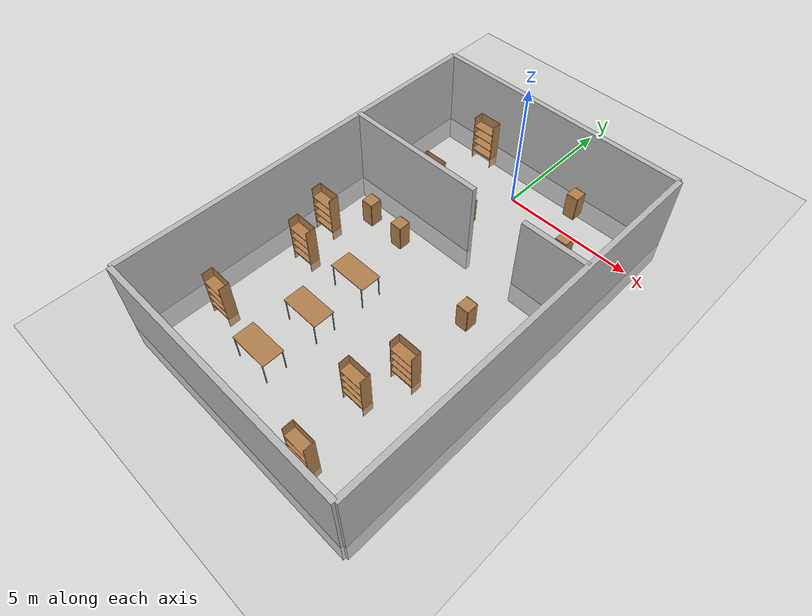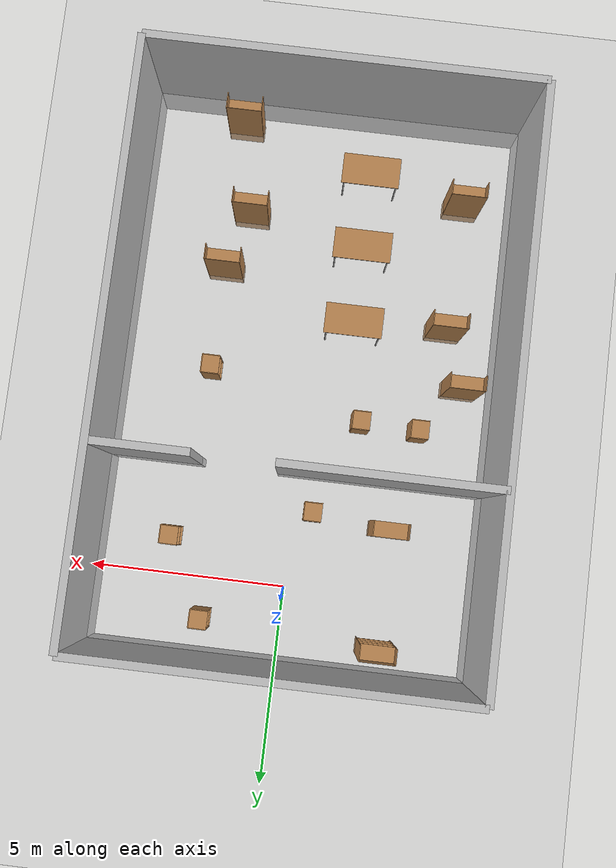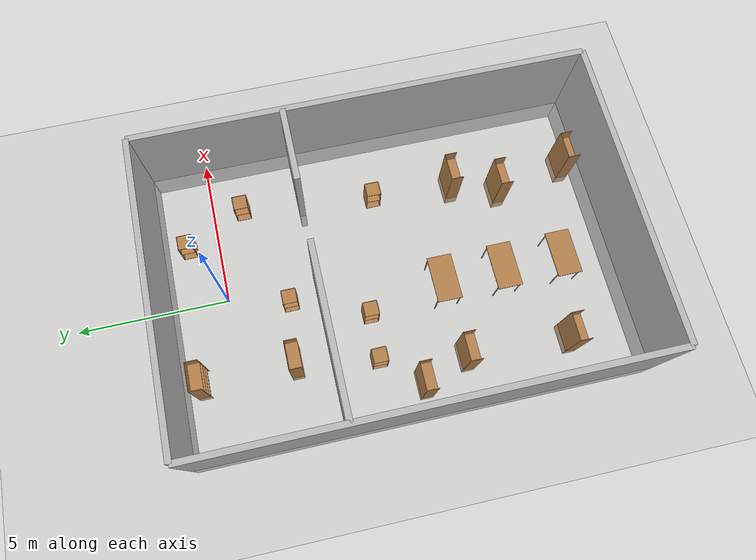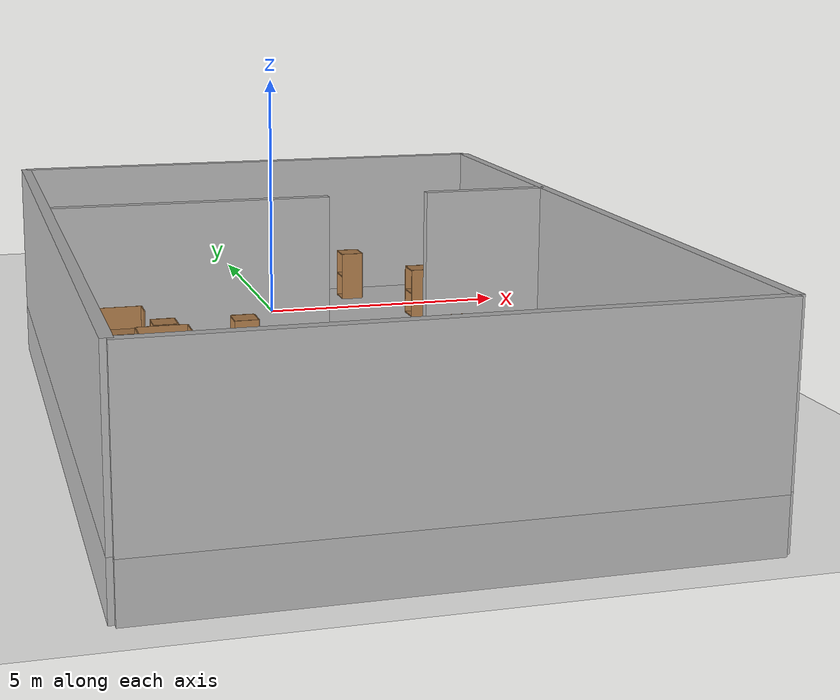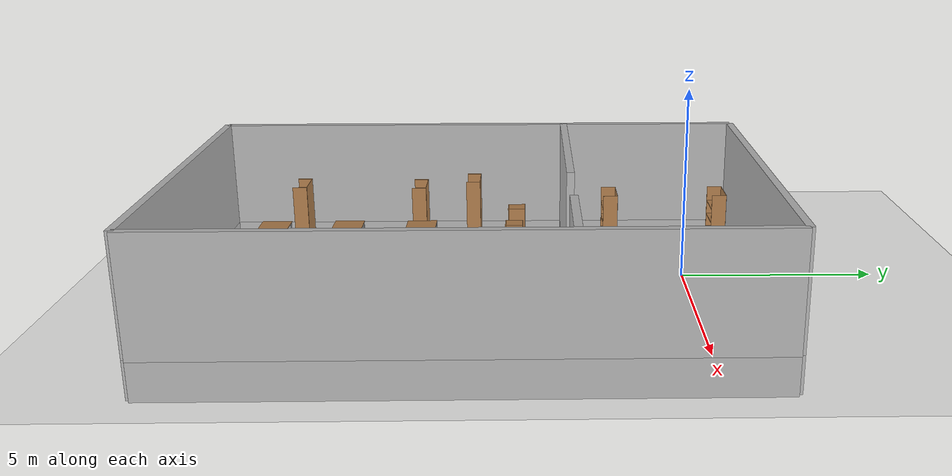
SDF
<sdf version="1.4">
 <world name="default">
  <physics type="ode">
   <gravity>0.000000 0.000000 -9.810000</gravity>
   <ode>
    <solver><type>quick</type><iters>20</iters><sor>1.000000</sor></solver>
    <constraints>
     <cfm>0.000000</cfm>
     <erp>0.200000</erp>
     <contact_max_correcting_vel>100.000000</contact_max_correcting_vel>
     <contact_surface_layer>0.000000</contact_surface_layer>
    </constraints>
   </ode>
   <real_time_update_rate>1000.000000</real_time_update_rate>
   <max_step_size>0.001000</max_step_size>
   <real_time_factor>1.000000</real_time_factor>
   <max_contacts>20</max_contacts>
  </physics>
  <plugin name="gz::sim::systems::Physics" filename="gz-sim-physics-system"/>
  <plugin name="gz::sim::systems::UserCommands" filename="gz-sim-user-commands-system"/>
  <plugin name="gz::sim::systems::SceneBroadcaster" filename="gz-sim-scene-broadcaster-system"/>
  <plugin name="gz::sim::systems::Contact" filename="gz-sim-contact-system"/>
  <plugin name="gz::sim::systems::Imu" filename="gz-sim-imu-system"/>
  <plugin name="gz::sim::systems::AirPressure" filename="gz-sim-air-pressure-system"/>
  <plugin name="gz::sim::systems::AirSpeed" filename="gz-sim-air-speed-system"/>
  <plugin name="gz::sim::systems::ApplyLinkWrench" filename="gz-sim-apply-link-wrench-system"/>
  <plugin name="gz::sim::systems::NavSat" filename="gz-sim-navsat-system"/>
  <plugin name="gz::sim::systems::Sensors" filename="gz-sim-sensors-system"/>
  <light name="sun" type="directional">
   <pose>0.000000 0.000000 10.000000 0.000000 0.000000 0.000000</pose>
   <diffuse>0.800000 0.800000 0.800000 1.000000</diffuse>
   <specular>0.200000 0.200000 0.200000 1.000000</specular>
   <attenuation>
    <range>1000.000000</range>
    <constant>0.900000</constant>
    <linear>0.010000</linear>
    <quadratic>0.001000</quadratic>
   </attenuation>
   <direction>0.500000 0.100000 -0.900000</direction>
  </light>
  <model name="ground_plane">
   <static>1</static>
   <link name="link">
    <collision name="collision">
     <geometry>
      <plane><normal>0.000000 0.000000 1.000000</normal><size>100.000000 100.000000</size></plane>
     </geometry>
     <surface><friction><ode><mu>100.000000</mu><mu2>50.000000</mu2></ode></friction></surface>
    </collision>
    <visual name="visual">
     <cast_shadows>0</cast_shadows>
     <geometry>
      <plane><normal>0.000000 0.000000 1.000000</normal><size>100.000000 100.000000</size></plane>
     </geometry>
     <material>
      <script><uri>file://media/materials/scripts/gazebo.material</uri><name>Gazebo/Grey</name></script>
     </material>
    </visual>
    <velocity_decay><linear>0.000000</linear><angular>0.000000</angular></velocity_decay>
   </link>
  </model>
  <model name="wall_1_model">
   <pose>0.0 -13.0 1.0 0.0 0.0 0.0</pose>
   <static>1</static>
   <link name="wall_1_body">
    <inertial>
     <mass>1.000000</mass>
     <inertia>
      <ixx>1.000000</ixx>
      <ixy>0.000000</ixy>
      <ixz>0.000000</ixz>
      <iyy>1.000000</iyy>
      <iyz>0.000000</iyz>
      <izz>1.000000</izz>
     </inertia>
    </inertial>
    <collision name="collision">
     <geometry><box><size>10.000000 0.200000 4.000000</size></box></geometry>
    </collision>
    <visual name="visual"><geometry><box><size>10.000000 0.200000 4.000000</size></box></geometry></visual>
    <velocity_decay><linear>0.000000</linear><angular>0.000000</angular></velocity_decay>
   </link>
  </model>
  <model name="wall_2_model">
   <pose>0.0 2.0 1.0 0.0 0.0 0.0</pose>
   <static>1</static>
   <link name="wall_2_body">
    <inertial>
     <mass>1.000000</mass>
     <inertia>
      <ixx>1.000000</ixx>
      <ixy>0.000000</ixy>
      <ixz>0.000000</ixz>
      <iyy>1.000000</iyy>
      <iyz>0.000000</iyz>
      <izz>1.000000</izz>
     </inertia>
    </inertial>
    <collision name="collision">
     <geometry><box><size>10.000000 0.200000 4.000000</size></box></geometry>
    </collision>
    <visual name="visual"><geometry><box><size>10.000000 0.200000 4.000000</size></box></geometry></visual>
    <velocity_decay><linear>0.000000</linear><angular>0.000000</angular></velocity_decay>
   </link>
  </model>
  <model name="wall_3_model">
   <pose>-5.0 -5.5 1.0 0.0 0.0 0.0</pose>
   <static>1</static>
   <link name="wall_3_body">
    <inertial>
     <mass>1.000000</mass>
     <inertia>
      <ixx>1.000000</ixx>
      <ixy>0.000000</ixy>
      <ixz>0.000000</ixz>
      <iyy>1.000000</iyy>
      <iyz>0.000000</iyz>
      <izz>1.000000</izz>
     </inertia>
    </inertial>
    <collision name="collision">
     <geometry><box><size>0.200000 15.000000 4.000000</size></box></geometry>
    </collision>
    <visual name="visual"><geometry><box><size>0.200000 15.000000 4.000000</size></box></geometry></visual>
    <velocity_decay><linear>0.000000</linear><angular>0.000000</angular></velocity_decay>
   </link>
  </model>
  <model name="wall_4_model">
   <pose>5.0 -5.5 1.0 0.0 0.0 0.0</pose>
   <static>1</static>
   <link name="wall_4_body">
    <inertial>
     <mass>1.000000</mass>
     <inertia>
      <ixx>1.000000</ixx>
      <ixy>0.000000</ixy>
      <ixz>0.000000</ixz>
      <iyy>1.000000</iyy>
      <iyz>0.000000</iyz>
      <izz>1.000000</izz>
     </inertia>
    </inertial>
    <collision name="collision">
     <geometry><box><size>0.200000 15.000000 4.000000</size></box></geometry>
    </collision>
    <visual name="visual"><geometry><box><size>0.200000 15.000000 4.000000</size></box></geometry></visual>
    <velocity_decay><linear>0.000000</linear><angular>0.000000</angular></velocity_decay>
   </link>
  </model>
  <model name="wall_5_model">
   <pose>-2.25 -3.0 1.0 0.0 0.0 0.0</pose>
   <static>1</static>
   <link name="wall_5_body">
    <inertial>
     <mass>1.000000</mass>
     <inertia>
      <ixx>1.000000</ixx>
      <ixy>0.000000</ixy>
      <ixz>0.000000</ixz>
      <iyy>1.000000</iyy>
      <iyz>0.000000</iyz>
      <izz>1.000000</izz>
     </inertia>
    </inertial>
    <collision name="collision">
     <geometry><box><size>5.500000 0.200000 4.000000</size></box></geometry>
    </collision>
    <visual name="visual"><geometry><box><size>5.500000 0.200000 4.000000</size></box></geometry></visual>
    <velocity_decay><linear>0.000000</linear><angular>0.000000</angular></velocity_decay>
   </link>
  </model>
  <model name="wall_6_model">
   <pose>3.75 -3.0 1.0 0.0 0.0 0.0</pose>
   <static>1</static>
   <link name="wall_6_body">
    <inertial>
     <mass>1.000000</mass>
     <inertia>
      <ixx>1.000000</ixx>
      <ixy>0.000000</ixy>
      <ixz>0.000000</ixz>
      <iyy>1.000000</iyy>
      <iyz>0.000000</iyz>
      <izz>1.000000</izz>
     </inertia>
    </inertial>
    <collision name="collision">
     <geometry><box><size>2.500000 0.200000 4.000000</size></box></geometry>
    </collision>
    <visual name="visual"><geometry><box><size>2.500000 0.200000 4.000000</size></box></geometry></visual>
    <velocity_decay><linear>0.000000</linear><angular>0.000000</angular></velocity_decay>
   </link>
  </model>
  <scene>
   <ambient>0.200000 0.200000 0.200000 1.000000</ambient>
   <background>0.700000 0.700000 0.700000 1.000000</background>
   <shadows>1</shadows>
  </scene>
  <model name="cabinet">
   <static>1</static>
   <link name="cabinet_bottom_plate">
    <inertial>
     <pose>0.000000 0.000000 -1.000000 0.000000 0.000000 0.000000</pose>
     <inertia>
      <ixx>2.050000</ixx>
      <ixy>0.000000</ixy>
      <ixz>0.000000</ixz>
      <iyy>2.050000</iyy>
      <iyz>0.000000</iyz>
      <izz>2.050000</izz>
     </inertia>
     <mass>25.000000</mass>
    </inertial>
    <collision name="cabinet_bottom_plate_geom">
     <pose>0.000000 0.000000 0.010000 0.000000 0.000000 0.000000</pose>
     <geometry><box><size>0.450000 0.450000 0.020000</size></box></geometry>
    </collision>
    <visual name="cabinet_bottom_plate_geom_visual">
     <pose>0.000000 0.000000 0.010000 0.000000 0.000000 0.000000</pose>
     <geometry><box><size>0.450000 0.450000 0.020000</size></box></geometry>
     <material>
      <script><uri>file://media/materials/scripts/gazebo.material</uri><name>Gazebo/Wood</name></script>
     </material>
    </visual>
    <collision name="cabinet_bottom_plate_geom_cabinet_back_plate">
     <pose>0.235000 0.000000 0.510000 0.000000 0.000000 0.000000</pose>
     <geometry><box><size>0.020000 0.450000 1.020000</size></box></geometry>
    </collision>
    <visual name="cabinet_bottom_plate_geom_cabinet_back_plate_visual">
     <pose>0.235000 0.000000 0.510000 0.000000 0.000000 0.000000</pose>
     <geometry><box><size>0.020000 0.450000 1.020000</size></box></geometry>
     <material>
      <script><uri>file://media/materials/scripts/gazebo.material</uri><name>Gazebo/Wood</name></script>
     </material>
    </visual>
    <collision name="cabinet_bottom_plate_geom_cabinet_left_plate">
     <pose>0.000000 0.235000 0.510000 0.000000 0.000000 0.000000</pose>
     <geometry><box><size>0.450000 0.020000 1.020000</size></box></geometry>
    </collision>
    <visual name="cabinet_bottom_plate_geom_cabinet_left_plate_visual">
     <pose>0.000000 0.235000 0.510000 0.000000 0.000000 0.000000</pose>
     <geometry><box><size>0.450000 0.020000 1.020000</size></box></geometry>
     <material>
      <script><uri>file://media/materials/scripts/gazebo.material</uri><name>Gazebo/Wood</name></script>
     </material>
    </visual>
    <collision name="cabinet_bottom_plate_geom_cabinet_middle_plate">
     <pose>0.000000 0.000000 0.510000 0.000000 0.000000 0.000000</pose>
     <geometry><box><size>0.450000 0.450000 0.020000</size></box></geometry>
    </collision>
    <visual name="cabinet_bottom_plate_geom_cabinet_middle_plate_visual">
     <pose>0.000000 0.000000 0.510000 0.000000 0.000000 0.000000</pose>
     <geometry><box><size>0.450000 0.450000 0.020000</size></box></geometry>
     <material>
      <script><uri>file://media/materials/scripts/gazebo.material</uri><name>Gazebo/Wood</name></script>
     </material>
    </visual>
    <collision name="cabinet_bottom_plate_geom_cabinet_right_plate">
     <pose>0.000000 -0.235000 0.510000 0.000000 0.000000 0.000000</pose>
     <geometry><box><size>0.450000 0.020000 1.020000</size></box></geometry>
    </collision>
    <visual name="cabinet_bottom_plate_geom_cabinet_right_plate_visual">
     <pose>0.000000 -0.235000 0.510000 0.000000 0.000000 0.000000</pose>
     <geometry><box><size>0.450000 0.020000 1.020000</size></box></geometry>
     <material>
      <script><uri>file://media/materials/scripts/gazebo.material</uri><name>Gazebo/Wood</name></script>
     </material>
    </visual>
    <collision name="cabinet_bottom_plate_geom_cabinet_top_plate">
     <pose>0.000000 0.000000 1.010000 0.000000 0.000000 0.000000</pose>
     <geometry><box><size>0.450000 0.450000 0.020000</size></box></geometry>
    </collision>
    <visual name="cabinet_bottom_plate_geom_cabinet_top_plate_visual">
     <pose>0.000000 0.000000 1.010000 0.000000 0.000000 0.000000</pose>
     <geometry><box><size>0.450000 0.450000 0.020000</size></box></geometry>
     <material>
      <script><uri>file://media/materials/scripts/gazebo.material</uri><name>Gazebo/Wood</name></script>
     </material>
    </visual>
    <velocity_decay><linear>0.000000</linear><angular>0.000000</angular></velocity_decay>
   </link>
   <pose>2.0 1.0 0.0 0.0 0.0 0.0</pose>
  </model>
  <model name="cabinet_0">
   <static>1</static>
   <link name="cabinet_bottom_plate">
    <inertial>
     <pose>0.000000 0.000000 -1.000000 0.000000 0.000000 0.000000</pose>
     <inertia>
      <ixx>2.050000</ixx>
      <ixy>0.000000</ixy>
      <ixz>0.000000</ixz>
      <iyy>2.050000</iyy>
      <iyz>0.000000</iyz>
      <izz>2.050000</izz>
     </inertia>
     <mass>25.000000</mass>
    </inertial>
    <collision name="cabinet_bottom_plate_geom">
     <pose>0.000000 0.000000 0.010000 0.000000 0.000000 0.000000</pose>
     <geometry><box><size>0.450000 0.450000 0.020000</size></box></geometry>
    </collision>
    <visual name="cabinet_bottom_plate_geom_visual">
     <pose>0.000000 0.000000 0.010000 0.000000 0.000000 0.000000</pose>
     <geometry><box><size>0.450000 0.450000 0.020000</size></box></geometry>
     <material>
      <script><uri>file://media/materials/scripts/gazebo.material</uri><name>Gazebo/Wood</name></script>
     </material>
    </visual>
    <collision name="cabinet_bottom_plate_geom_cabinet_back_plate">
     <pose>0.235000 0.000000 0.510000 0.000000 0.000000 0.000000</pose>
     <geometry><box><size>0.020000 0.450000 1.020000</size></box></geometry>
    </collision>
    <visual name="cabinet_bottom_plate_geom_cabinet_back_plate_visual">
     <pose>0.235000 0.000000 0.510000 0.000000 0.000000 0.000000</pose>
     <geometry><box><size>0.020000 0.450000 1.020000</size></box></geometry>
     <material>
      <script><uri>file://media/materials/scripts/gazebo.material</uri><name>Gazebo/Wood</name></script>
     </material>
    </visual>
    <collision name="cabinet_bottom_plate_geom_cabinet_left_plate">
     <pose>0.000000 0.235000 0.510000 0.000000 0.000000 0.000000</pose>
     <geometry><box><size>0.450000 0.020000 1.020000</size></box></geometry>
    </collision>
    <visual name="cabinet_bottom_plate_geom_cabinet_left_plate_visual">
     <pose>0.000000 0.235000 0.510000 0.000000 0.000000 0.000000</pose>
     <geometry><box><size>0.450000 0.020000 1.020000</size></box></geometry>
     <material>
      <script><uri>file://media/materials/scripts/gazebo.material</uri><name>Gazebo/Wood</name></script>
     </material>
    </visual>
    <collision name="cabinet_bottom_plate_geom_cabinet_middle_plate">
     <pose>0.000000 0.000000 0.510000 0.000000 0.000000 0.000000</pose>
     <geometry><box><size>0.450000 0.450000 0.020000</size></box></geometry>
    </collision>
    <visual name="cabinet_bottom_plate_geom_cabinet_middle_plate_visual">
     <pose>0.000000 0.000000 0.510000 0.000000 0.000000 0.000000</pose>
     <geometry><box><size>0.450000 0.450000 0.020000</size></box></geometry>
     <material>
      <script><uri>file://media/materials/scripts/gazebo.material</uri><name>Gazebo/Wood</name></script>
     </material>
    </visual>
    <collision name="cabinet_bottom_plate_geom_cabinet_right_plate">
     <pose>0.000000 -0.235000 0.510000 0.000000 0.000000 0.000000</pose>
     <geometry><box><size>0.450000 0.020000 1.020000</size></box></geometry>
    </collision>
    <visual name="cabinet_bottom_plate_geom_cabinet_right_plate_visual">
     <pose>0.000000 -0.235000 0.510000 0.000000 0.000000 0.000000</pose>
     <geometry><box><size>0.450000 0.020000 1.020000</size></box></geometry>
     <material>
      <script><uri>file://media/materials/scripts/gazebo.material</uri><name>Gazebo/Wood</name></script>
     </material>
    </visual>
    <collision name="cabinet_bottom_plate_geom_cabinet_top_plate">
     <pose>0.000000 0.000000 1.010000 0.000000 0.000000 0.000000</pose>
     <geometry><box><size>0.450000 0.450000 0.020000</size></box></geometry>
    </collision>
    <visual name="cabinet_bottom_plate_geom_cabinet_top_plate_visual">
     <pose>0.000000 0.000000 1.010000 0.000000 0.000000 0.000000</pose>
     <geometry><box><size>0.450000 0.450000 0.020000</size></box></geometry>
     <material>
      <script><uri>file://media/materials/scripts/gazebo.material</uri><name>Gazebo/Wood</name></script>
     </material>
    </visual>
    <velocity_decay><linear>0.000000</linear><angular>0.000000</angular></velocity_decay>
   </link>
   <pose>2.51573 -5.43949 0.0 0.0 0.0 0.0</pose>
  </model>
  <model name="bookshelf">
   <static>1</static>
   <link name="link">
    <inertial><mass>1.000000</mass></inertial>
    <collision name="back">
     <pose>0.000000 0.005000 0.600000 0.000000 0.000000 0.000000</pose>
     <geometry><box><size>0.900000 0.010000 2.00000</size></box></geometry>
    </collision>
    <visual name="visual1">
     <pose>0.000000 0.005000 0.600000 0.000000 0.000000 0.000000</pose>
     <geometry><box><size>0.900000 0.010000 2.00000</size></box></geometry>
     <material>
      <script><uri>file://media/materials/scripts/gazebo.material</uri><name>Gazebo/Wood</name></script>
     </material>
    </visual>
    <collision name="left_side">
     <pose>0.450000 -0.195000 0.600000 0.000000 0.000000 0.000000</pose>
     <geometry><box><size>0.020000 0.400000 2.00000</size></box></geometry>
    </collision>
    <visual name="visual2">
     <pose>0.450000 -0.195000 0.600000 0.000000 0.000000 0.000000</pose>
     <geometry><box><size>0.020000 0.400000 2.00000</size></box></geometry>
     <material>
      <script><uri>file://media/materials/scripts/gazebo.material</uri><name>Gazebo/Wood</name></script>
     </material>
    </visual>
    <collision name="right_side">
     <pose>-0.450000 -0.195000 0.600000 0.000000 0.000000 0.000000</pose>
     <geometry><box><size>0.020000 0.400000 2.00000</size></box></geometry>
    </collision>
    <visual name="visual3">
     <pose>-0.450000 -0.195000 0.600000 0.000000 0.000000 0.000000</pose>
     <geometry><box><size>0.020000 0.400000 2.00000</size></box></geometry>
     <material>
      <script><uri>file://media/materials/scripts/gazebo.material</uri><name>Gazebo/Wood</name></script>
     </material>
    </visual>
    <collision name="bottom">
     <pose>0.000000 -0.195000 0.030000 0.000000 0.000000 0.000000</pose>
     <geometry><box><size>0.880000 0.400000 0.060000</size></box></geometry>
    </collision>
    <visual name="visual4">
     <pose>0.000000 -0.195000 0.030000 0.000000 0.000000 0.000000</pose>
     <geometry><box><size>0.880000 0.400000 0.060000</size></box></geometry>
     <material>
      <script><uri>file://media/materials/scripts/gazebo.material</uri><name>Gazebo/Wood</name></script>
     </material>
    </visual>
    <collision name="top">
     <pose>0.000000 -0.195000 1.190000 0.000000 0.000000 0.000000</pose>
     <geometry><box><size>0.880000 0.400000 0.020000</size></box></geometry>
    </collision>
    <visual name="visual5">
     <pose>0.000000 -0.195000 1.190000 0.000000 0.000000 0.000000</pose>
     <geometry><box><size>0.880000 0.400000 0.020000</size></box></geometry>
     <material>
      <script><uri>file://media/materials/scripts/gazebo.material</uri><name>Gazebo/Wood</name></script>
     </material>
    </visual>
    <collision name="low_shelf">
     <pose>0.000000 -0.195000 0.430000 0.000000 0.000000 0.000000</pose>
     <geometry><box><size>0.880000 0.400000 0.020000</size></box></geometry>
    </collision>
    <visual name="visual6">
     <pose>0.000000 -0.195000 0.430000 0.000000 0.000000 0.000000</pose>
     <geometry><box><size>0.880000 0.400000 0.020000</size></box></geometry>
     <material>
      <script><uri>file://media/materials/scripts/gazebo.material</uri><name>Gazebo/Wood</name></script>
     </material>
    </visual>
    <collision name="high_shelf">
     <pose>0.000000 -0.195000 0.800000 0.000000 0.000000 0.000000</pose>
     <geometry><box><size>0.880000 0.400000 0.020000</size></box></geometry>
    </collision>
    <visual name="visual7">
     <pose>0.000000 -0.195000 0.800000 0.000000 0.000000 0.000000</pose>
     <geometry><box><size>0.880000 0.400000 0.020000</size></box></geometry>
     <material>
      <script><uri>file://media/materials/scripts/gazebo.material</uri><name>Gazebo/Wood</name></script>
     </material>
    </visual>
    <velocity_decay><linear>0.000000</linear><angular>0.000000</angular></velocity_decay>
   </link>
   <pose>2.0 -9.55401 0.0 0.0 0.0 0.0</pose>
  </model>
  <model name="bookshelf_0">
   <static>1</static>
   <link name="link">
    <inertial><mass>1.000000</mass></inertial>
    <collision name="back">
     <pose>0.000000 0.005000 0.600000 0.000000 0.000000 0.000000</pose>
     <geometry><box><size>0.900000 0.010000 2.00000</size></box></geometry>
    </collision>
    <visual name="visual1">
     <pose>0.000000 0.005000 0.600000 0.000000 0.000000 0.000000</pose>
     <geometry><box><size>0.900000 0.010000 2.00000</size></box></geometry>
     <material>
      <script><uri>file://media/materials/scripts/gazebo.material</uri><name>Gazebo/Wood</name></script>
     </material>
    </visual>
    <collision name="left_side">
     <pose>0.450000 -0.195000 0.600000 0.000000 0.000000 0.000000</pose>
     <geometry><box><size>0.020000 0.400000 2.00000</size></box></geometry>
    </collision>
    <visual name="visual2">
     <pose>0.450000 -0.195000 0.600000 0.000000 0.000000 0.000000</pose>
     <geometry><box><size>0.020000 0.400000 2.00000</size></box></geometry>
     <material>
      <script><uri>file://media/materials/scripts/gazebo.material</uri><name>Gazebo/Wood</name></script>
     </material>
    </visual>
    <collision name="right_side">
     <pose>-0.450000 -0.195000 0.600000 0.000000 0.000000 0.000000</pose>
     <geometry><box><size>0.020000 0.400000 2.00000</size></box></geometry>
    </collision>
    <visual name="visual3">
     <pose>-0.450000 -0.195000 0.600000 0.000000 0.000000 0.000000</pose>
     <geometry><box><size>0.020000 0.400000 2.00000</size></box></geometry>
     <material>
      <script><uri>file://media/materials/scripts/gazebo.material</uri><name>Gazebo/Wood</name></script>
     </material>
    </visual>
    <collision name="bottom">
     <pose>0.000000 -0.195000 0.030000 0.000000 0.000000 0.000000</pose>
     <geometry><box><size>0.880000 0.400000 0.060000</size></box></geometry>
    </collision>
    <visual name="visual4">
     <pose>0.000000 -0.195000 0.030000 0.000000 0.000000 0.000000</pose>
     <geometry><box><size>0.880000 0.400000 0.060000</size></box></geometry>
     <material>
      <script><uri>file://media/materials/scripts/gazebo.material</uri><name>Gazebo/Wood</name></script>
     </material>
    </visual>
    <collision name="top">
     <pose>0.000000 -0.195000 1.190000 0.000000 0.000000 0.000000</pose>
     <geometry><box><size>0.880000 0.400000 0.020000</size></box></geometry>
    </collision>
    <visual name="visual5">
     <pose>0.000000 -0.195000 1.190000 0.000000 0.000000 0.000000</pose>
     <geometry><box><size>0.880000 0.400000 0.020000</size></box></geometry>
     <material>
      <script><uri>file://media/materials/scripts/gazebo.material</uri><name>Gazebo/Wood</name></script>
     </material>
    </visual>
    <collision name="low_shelf">
     <pose>0.000000 -0.195000 0.430000 0.000000 0.000000 0.000000</pose>
     <geometry><box><size>0.880000 0.400000 0.020000</size></box></geometry>
    </collision>
    <visual name="visual6">
     <pose>0.000000 -0.195000 0.430000 0.000000 0.000000 0.000000</pose>
     <geometry><box><size>0.880000 0.400000 0.020000</size></box></geometry>
     <material>
      <script><uri>file://media/materials/scripts/gazebo.material</uri><name>Gazebo/Wood</name></script>
     </material>
    </visual>
    <collision name="high_shelf">
     <pose>0.000000 -0.195000 0.800000 0.000000 0.000000 0.000000</pose>
     <geometry><box><size>0.880000 0.400000 0.020000</size></box></geometry>
    </collision>
    <visual name="visual7">
     <pose>0.000000 -0.195000 0.800000 0.000000 0.000000 0.000000</pose>
     <geometry><box><size>0.880000 0.400000 0.020000</size></box></geometry>
     <material>
      <script><uri>file://media/materials/scripts/gazebo.material</uri><name>Gazebo/Wood</name></script>
     </material>
    </visual>
    <velocity_decay><linear>0.000000</linear><angular>0.000000</angular></velocity_decay>
   </link>
   <pose>-2.49657 -1.57894 0.0 0.0 0.0 0.0</pose>
  </model>
  <model name="bookshelf_1">
   <static>1</static>
   <link name="link">
    <inertial><mass>1.000000</mass></inertial>
    <collision name="back">
     <pose>0.000000 0.005000 0.600000 0.000000 0.000000 0.000000</pose>
     <geometry><box><size>0.900000 0.010000 2.00000</size></box></geometry>
    </collision>
    <visual name="visual1">
     <pose>0.000000 0.005000 0.600000 0.000000 0.000000 0.000000</pose>
     <geometry><box><size>0.900000 0.010000 2.00000</size></box></geometry>
     <material>
      <script><uri>file://media/materials/scripts/gazebo.material</uri><name>Gazebo/Wood</name></script>
     </material>
    </visual>
    <collision name="left_side">
     <pose>0.450000 -0.195000 0.600000 0.000000 0.000000 0.000000</pose>
     <geometry><box><size>0.020000 0.400000 2.00000</size></box></geometry>
    </collision>
    <visual name="visual2">
     <pose>0.450000 -0.195000 0.600000 0.000000 0.000000 0.000000</pose>
     <geometry><box><size>0.020000 0.400000 2.00000</size></box></geometry>
     <material>
      <script><uri>file://media/materials/scripts/gazebo.material</uri><name>Gazebo/Wood</name></script>
     </material>
    </visual>
    <collision name="right_side">
     <pose>-0.450000 -0.195000 0.600000 0.000000 0.000000 0.000000</pose>
     <geometry><box><size>0.020000 0.400000 2.00000</size></box></geometry>
    </collision>
    <visual name="visual3">
     <pose>-0.450000 -0.195000 0.600000 0.000000 0.000000 0.000000</pose>
     <geometry><box><size>0.020000 0.400000 2.00000</size></box></geometry>
     <material>
      <script><uri>file://media/materials/scripts/gazebo.material</uri><name>Gazebo/Wood</name></script>
     </material>
    </visual>
    <collision name="bottom">
     <pose>0.000000 -0.195000 0.030000 0.000000 0.000000 0.000000</pose>
     <geometry><box><size>0.880000 0.400000 0.060000</size></box></geometry>
    </collision>
    <visual name="visual4">
     <pose>0.000000 -0.195000 0.030000 0.000000 0.000000 0.000000</pose>
     <geometry><box><size>0.880000 0.400000 0.060000</size></box></geometry>
     <material>
      <script><uri>file://media/materials/scripts/gazebo.material</uri><name>Gazebo/Wood</name></script>
     </material>
    </visual>
    <collision name="top">
     <pose>0.000000 -0.195000 1.190000 0.000000 0.000000 0.000000</pose>
     <geometry><box><size>0.880000 0.400000 0.020000</size></box></geometry>
    </collision>
    <visual name="visual5">
     <pose>0.000000 -0.195000 1.190000 0.000000 0.000000 0.000000</pose>
     <geometry><box><size>0.880000 0.400000 0.020000</size></box></geometry>
     <material>
      <script><uri>file://media/materials/scripts/gazebo.material</uri><name>Gazebo/Wood</name></script>
     </material>
    </visual>
    <collision name="low_shelf">
     <pose>0.000000 -0.195000 0.430000 0.000000 0.000000 0.000000</pose>
     <geometry><box><size>0.880000 0.400000 0.020000</size></box></geometry>
    </collision>
    <visual name="visual6">
     <pose>0.000000 -0.195000 0.430000 0.000000 0.000000 0.000000</pose>
     <geometry><box><size>0.880000 0.400000 0.020000</size></box></geometry>
     <material>
      <script><uri>file://media/materials/scripts/gazebo.material</uri><name>Gazebo/Wood</name></script>
     </material>
    </visual>
    <collision name="high_shelf">
     <pose>0.000000 -0.195000 0.800000 0.000000 0.000000 0.000000</pose>
     <geometry><box><size>0.880000 0.400000 0.020000</size></box></geometry>
    </collision>
    <visual name="visual7">
     <pose>0.000000 -0.195000 0.800000 0.000000 0.000000 0.000000</pose>
     <geometry><box><size>0.880000 0.400000 0.020000</size></box></geometry>
     <material>
      <script><uri>file://media/materials/scripts/gazebo.material</uri><name>Gazebo/Wood</name></script>
     </material>
    </visual>
    <velocity_decay><linear>0.000000</linear><angular>0.000000</angular></velocity_decay>
   </link>
   <pose>-2.49816 1.46785 0.0 0.0 0.0 0.0</pose>
  </model>
  <model name="table">
   <static>1</static>
   <link name="link">
    <collision name="surface">
     <pose>0.000000 0.000000 1.000000 0.000000 0.000000 0.000000</pose>
     <geometry><box><size>1.500000 0.800000 0.030000</size></box></geometry>
    </collision>
    <visual name="visual1">
     <pose>0.000000 0.000000 1.000000 0.000000 0.000000 0.000000</pose>
     <geometry><box><size>1.500000 0.800000 0.030000</size></box></geometry>
     <material>
      <script><uri>file://media/materials/scripts/gazebo.material</uri><name>Gazebo/Wood</name></script>
     </material>
    </visual>
    <collision name="front_left_leg">
     <pose>0.680000 0.380000 0.500000 0.000000 0.000000 0.000000</pose>
     <geometry><cylinder><radius>0.020000</radius><length>1.000000</length></cylinder></geometry>
    </collision>
    <visual name="front_left_leg">
     <pose>0.680000 0.380000 0.500000 0.000000 0.000000 0.000000</pose>
     <geometry><cylinder><radius>0.020000</radius><length>1.000000</length></cylinder></geometry>
     <material>
      <script><uri>file://media/materials/scripts/gazebo.material</uri><name>Gazebo/Grey</name></script>
     </material>
    </visual>
    <collision name="front_right_leg">
     <pose>0.680000 -0.380000 0.500000 0.000000 0.000000 0.000000</pose>
     <geometry><cylinder><radius>0.020000</radius><length>1.000000</length></cylinder></geometry>
    </collision>
    <visual name="front_right_leg">
     <pose>0.680000 -0.380000 0.500000 0.000000 0.000000 0.000000</pose>
     <geometry><cylinder><radius>0.020000</radius><length>1.000000</length></cylinder></geometry>
     <material>
      <script><uri>file://media/materials/scripts/gazebo.material</uri><name>Gazebo/Grey</name></script>
     </material>
    </visual>
    <collision name="back_right_leg">
     <pose>-0.680000 -0.380000 0.500000 0.000000 0.000000 0.000000</pose>
     <geometry><cylinder><radius>0.020000</radius><length>1.000000</length></cylinder></geometry>
    </collision>
    <visual name="back_right_leg">
     <pose>-0.680000 -0.380000 0.500000 0.000000 0.000000 0.000000</pose>
     <geometry><cylinder><radius>0.020000</radius><length>1.000000</length></cylinder></geometry>
     <material>
      <script><uri>file://media/materials/scripts/gazebo.material</uri><name>Gazebo/Grey</name></script>
     </material>
    </visual>
    <collision name="back_left_leg">
     <pose>-0.680000 0.380000 0.500000 0.000000 0.000000 0.000000</pose>
     <geometry><cylinder><radius>0.020000</radius><length>1.000000</length></cylinder></geometry>
    </collision>
    <visual name="back_left_leg">
     <pose>-0.680000 0.380000 0.500000 0.000000 0.000000 0.000000</pose>
     <geometry><cylinder><radius>0.020000</radius><length>1.000000</length></cylinder></geometry>
     <material>
      <script><uri>file://media/materials/scripts/gazebo.material</uri><name>Gazebo/Grey</name></script>
     </material>
    </visual>
    <velocity_decay><linear>0.000000</linear><angular>0.000000</angular></velocity_decay>
   </link>
   <pose>-1.0 -9.0 0.0 0.0 0.0 0.0</pose>
  </model>
  <model name="cabinet_1">
   <static>1</static>
   <link name="cabinet_bottom_plate">
    <inertial>
     <pose>0.000000 0.000000 -1.000000 0.000000 0.000000 0.000000</pose>
     <inertia>
      <ixx>2.050000</ixx>
      <ixy>0.000000</ixy>
      <ixz>0.000000</ixz>
      <iyy>2.050000</iyy>
      <iyz>0.000000</iyz>
      <izz>2.050000</izz>
     </inertia>
     <mass>25.000000</mass>
    </inertial>
    <collision name="cabinet_bottom_plate_geom">
     <pose>0.000000 0.000000 0.010000 0.000000 0.000000 0.000000</pose>
     <geometry><box><size>0.450000 0.450000 0.020000</size></box></geometry>
    </collision>
    <visual name="cabinet_bottom_plate_geom_visual">
     <pose>0.000000 0.000000 0.010000 0.000000 0.000000 0.000000</pose>
     <geometry><box><size>0.450000 0.450000 0.020000</size></box></geometry>
     <material>
      <script><uri>file://media/materials/scripts/gazebo.material</uri><name>Gazebo/Wood</name></script>
     </material>
    </visual>
    <collision name="cabinet_bottom_plate_geom_cabinet_back_plate">
     <pose>0.235000 0.000000 0.510000 0.000000 0.000000 0.000000</pose>
     <geometry><box><size>0.020000 0.450000 1.020000</size></box></geometry>
    </collision>
    <visual name="cabinet_bottom_plate_geom_cabinet_back_plate_visual">
     <pose>0.235000 0.000000 0.510000 0.000000 0.000000 0.000000</pose>
     <geometry><box><size>0.020000 0.450000 1.020000</size></box></geometry>
     <material>
      <script><uri>file://media/materials/scripts/gazebo.material</uri><name>Gazebo/Wood</name></script>
     </material>
    </visual>
    <collision name="cabinet_bottom_plate_geom_cabinet_left_plate">
     <pose>0.000000 0.235000 0.510000 0.000000 0.000000 0.000000</pose>
     <geometry><box><size>0.450000 0.020000 1.020000</size></box></geometry>
    </collision>
    <visual name="cabinet_bottom_plate_geom_cabinet_left_plate_visual">
     <pose>0.000000 0.235000 0.510000 0.000000 0.000000 0.000000</pose>
     <geometry><box><size>0.450000 0.020000 1.020000</size></box></geometry>
     <material>
      <script><uri>file://media/materials/scripts/gazebo.material</uri><name>Gazebo/Wood</name></script>
     </material>
    </visual>
    <collision name="cabinet_bottom_plate_geom_cabinet_middle_plate">
     <pose>0.000000 0.000000 0.510000 0.000000 0.000000 0.000000</pose>
     <geometry><box><size>0.450000 0.450000 0.020000</size></box></geometry>
    </collision>
    <visual name="cabinet_bottom_plate_geom_cabinet_middle_plate_visual">
     <pose>0.000000 0.000000 0.510000 0.000000 0.000000 0.000000</pose>
     <geometry><box><size>0.450000 0.450000 0.020000</size></box></geometry>
     <material>
      <script><uri>file://media/materials/scripts/gazebo.material</uri><name>Gazebo/Wood</name></script>
     </material>
    </visual>
    <collision name="cabinet_bottom_plate_geom_cabinet_right_plate">
     <pose>0.000000 -0.235000 0.510000 0.000000 0.000000 0.000000</pose>
     <geometry><box><size>0.450000 0.020000 1.020000</size></box></geometry>
    </collision>
    <visual name="cabinet_bottom_plate_geom_cabinet_right_plate_visual">
     <pose>0.000000 -0.235000 0.510000 0.000000 0.000000 0.000000</pose>
     <geometry><box><size>0.450000 0.020000 1.020000</size></box></geometry>
     <material>
      <script><uri>file://media/materials/scripts/gazebo.material</uri><name>Gazebo/Wood</name></script>
     </material>
    </visual>
    <collision name="cabinet_bottom_plate_geom_cabinet_top_plate">
     <pose>0.000000 0.000000 1.010000 0.000000 0.000000 0.000000</pose>
     <geometry><box><size>0.450000 0.450000 0.020000</size></box></geometry>
    </collision>
    <visual name="cabinet_bottom_plate_geom_cabinet_top_plate_visual">
     <pose>0.000000 0.000000 1.010000 0.000000 0.000000 0.000000</pose>
     <geometry><box><size>0.450000 0.450000 0.020000</size></box></geometry>
     <material>
      <script><uri>file://media/materials/scripts/gazebo.material</uri><name>Gazebo/Wood</name></script>
     </material>
    </visual>
    <velocity_decay><linear>0.000000</linear><angular>0.000000</angular></velocity_decay>
   </link>
   <pose>-3.0 -4.40005 0.0 0.0 0.0 0.0</pose>
  </model>
  <model name="cabinet_2">
   <static>1</static>
   <link name="cabinet_bottom_plate">
    <inertial>
     <pose>0.000000 0.000000 -1.000000 0.000000 0.000000 0.000000</pose>
     <inertia>
      <ixx>2.050000</ixx>
      <ixy>0.000000</ixy>
      <ixz>0.000000</ixz>
      <iyy>2.050000</iyy>
      <iyz>0.000000</iyz>
      <izz>2.050000</izz>
     </inertia>
     <mass>25.000000</mass>
    </inertial>
    <collision name="cabinet_bottom_plate_geom">
     <pose>0.000000 0.000000 0.010000 0.000000 0.000000 0.000000</pose>
     <geometry><box><size>0.450000 0.450000 0.020000</size></box></geometry>
    </collision>
    <visual name="cabinet_bottom_plate_geom_visual">
     <pose>0.000000 0.000000 0.010000 0.000000 0.000000 0.000000</pose>
     <geometry><box><size>0.450000 0.450000 0.020000</size></box></geometry>
     <material>
      <script><uri>file://media/materials/scripts/gazebo.material</uri><name>Gazebo/Wood</name></script>
     </material>
    </visual>
    <collision name="cabinet_bottom_plate_geom_cabinet_back_plate">
     <pose>0.235000 0.000000 0.510000 0.000000 0.000000 0.000000</pose>
     <geometry><box><size>0.020000 0.450000 1.020000</size></box></geometry>
    </collision>
    <visual name="cabinet_bottom_plate_geom_cabinet_back_plate_visual">
     <pose>0.235000 0.000000 0.510000 0.000000 0.000000 0.000000</pose>
     <geometry><box><size>0.020000 0.450000 1.020000</size></box></geometry>
     <material>
      <script><uri>file://media/materials/scripts/gazebo.material</uri><name>Gazebo/Wood</name></script>
     </material>
    </visual>
    <collision name="cabinet_bottom_plate_geom_cabinet_left_plate">
     <pose>0.000000 0.235000 0.510000 0.000000 0.000000 0.000000</pose>
     <geometry><box><size>0.450000 0.020000 1.020000</size></box></geometry>
    </collision>
    <visual name="cabinet_bottom_plate_geom_cabinet_left_plate_visual">
     <pose>0.000000 0.235000 0.510000 0.000000 0.000000 0.000000</pose>
     <geometry><box><size>0.450000 0.020000 1.020000</size></box></geometry>
     <material>
      <script><uri>file://media/materials/scripts/gazebo.material</uri><name>Gazebo/Wood</name></script>
     </material>
    </visual>
    <collision name="cabinet_bottom_plate_geom_cabinet_middle_plate">
     <pose>0.000000 0.000000 0.510000 0.000000 0.000000 0.000000</pose>
     <geometry><box><size>0.450000 0.450000 0.020000</size></box></geometry>
    </collision>
    <visual name="cabinet_bottom_plate_geom_cabinet_middle_plate_visual">
     <pose>0.000000 0.000000 0.510000 0.000000 0.000000 0.000000</pose>
     <geometry><box><size>0.450000 0.450000 0.020000</size></box></geometry>
     <material>
      <script><uri>file://media/materials/scripts/gazebo.material</uri><name>Gazebo/Wood</name></script>
     </material>
    </visual>
    <collision name="cabinet_bottom_plate_geom_cabinet_right_plate">
     <pose>0.000000 -0.235000 0.510000 0.000000 0.000000 0.000000</pose>
     <geometry><box><size>0.450000 0.020000 1.020000</size></box></geometry>
    </collision>
    <visual name="cabinet_bottom_plate_geom_cabinet_right_plate_visual">
     <pose>0.000000 -0.235000 0.510000 0.000000 0.000000 0.000000</pose>
     <geometry><box><size>0.450000 0.020000 1.020000</size></box></geometry>
     <material>
      <script><uri>file://media/materials/scripts/gazebo.material</uri><name>Gazebo/Wood</name></script>
     </material>
    </visual>
    <collision name="cabinet_bottom_plate_geom_cabinet_top_plate">
     <pose>0.000000 0.000000 1.010000 0.000000 0.000000 0.000000</pose>
     <geometry><box><size>0.450000 0.450000 0.020000</size></box></geometry>
    </collision>
    <visual name="cabinet_bottom_plate_geom_cabinet_top_plate_visual">
     <pose>0.000000 0.000000 1.010000 0.000000 0.000000 0.000000</pose>
     <geometry><box><size>0.450000 0.450000 0.020000</size></box></geometry>
     <material>
      <script><uri>file://media/materials/scripts/gazebo.material</uri><name>Gazebo/Wood</name></script>
     </material>
    </visual>
    <velocity_decay><linear>0.000000</linear><angular>0.000000</angular></velocity_decay>
   </link>
   <pose>-1.49183 -4.45622 0.0 0.0 0.0 0.0</pose>
  </model>
  <model name="bookshelf_2">
   <static>1</static>
   <link name="link">
    <inertial><mass>1.000000</mass></inertial>
    <collision name="back">
     <pose>0.000000 0.005000 0.600000 0.000000 0.000000 0.000000</pose>
     <geometry><box><size>0.900000 0.010000 2.00000</size></box></geometry>
    </collision>
    <visual name="visual1">
     <pose>0.000000 0.005000 0.600000 0.000000 0.000000 0.000000</pose>
     <geometry><box><size>0.900000 0.010000 2.00000</size></box></geometry>
     <material>
      <script><uri>file://media/materials/scripts/gazebo.material</uri><name>Gazebo/Wood</name></script>
     </material>
    </visual>
    <collision name="left_side">
     <pose>0.450000 -0.195000 0.600000 0.000000 0.000000 0.000000</pose>
     <geometry><box><size>0.020000 0.400000 2.00000</size></box></geometry>
    </collision>
    <visual name="visual2">
     <pose>0.450000 -0.195000 0.600000 0.000000 0.000000 0.000000</pose>
     <geometry><box><size>0.020000 0.400000 2.00000</size></box></geometry>
     <material>
      <script><uri>file://media/materials/scripts/gazebo.material</uri><name>Gazebo/Wood</name></script>
     </material>
    </visual>
    <collision name="right_side">
     <pose>-0.450000 -0.195000 0.600000 0.000000 0.000000 0.000000</pose>
     <geometry><box><size>0.020000 0.400000 2.00000</size></box></geometry>
    </collision>
    <visual name="visual3">
     <pose>-0.450000 -0.195000 0.600000 0.000000 0.000000 0.000000</pose>
     <geometry><box><size>0.020000 0.400000 2.00000</size></box></geometry>
     <material>
      <script><uri>file://media/materials/scripts/gazebo.material</uri><name>Gazebo/Wood</name></script>
     </material>
    </visual>
    <collision name="bottom">
     <pose>0.000000 -0.195000 0.030000 0.000000 0.000000 0.000000</pose>
     <geometry><box><size>0.880000 0.400000 0.060000</size></box></geometry>
    </collision>
    <visual name="visual4">
     <pose>0.000000 -0.195000 0.030000 0.000000 0.000000 0.000000</pose>
     <geometry><box><size>0.880000 0.400000 0.060000</size></box></geometry>
     <material>
      <script><uri>file://media/materials/scripts/gazebo.material</uri><name>Gazebo/Wood</name></script>
     </material>
    </visual>
    <collision name="top">
     <pose>0.000000 -0.195000 1.190000 0.000000 0.000000 0.000000</pose>
     <geometry><box><size>0.880000 0.400000 0.020000</size></box></geometry>
    </collision>
    <visual name="visual5">
     <pose>0.000000 -0.195000 1.190000 0.000000 0.000000 0.000000</pose>
     <geometry><box><size>0.880000 0.400000 0.020000</size></box></geometry>
     <material>
      <script><uri>file://media/materials/scripts/gazebo.material</uri><name>Gazebo/Wood</name></script>
     </material>
    </visual>
    <collision name="low_shelf">
     <pose>0.000000 -0.195000 0.430000 0.000000 0.000000 0.000000</pose>
     <geometry><box><size>0.880000 0.400000 0.020000</size></box></geometry>
    </collision>
    <visual name="visual6">
     <pose>0.000000 -0.195000 0.430000 0.000000 0.000000 0.000000</pose>
     <geometry><box><size>0.880000 0.400000 0.020000</size></box></geometry>
     <material>
      <script><uri>file://media/materials/scripts/gazebo.material</uri><name>Gazebo/Wood</name></script>
     </material>
    </visual>
    <collision name="high_shelf">
     <pose>0.000000 -0.195000 0.800000 0.000000 0.000000 0.000000</pose>
     <geometry><box><size>0.880000 0.400000 0.020000</size></box></geometry>
    </collision>
    <visual name="visual7">
     <pose>0.000000 -0.195000 0.800000 0.000000 0.000000 0.000000</pose>
     <geometry><box><size>0.880000 0.400000 0.020000</size></box></geometry>
     <material>
      <script><uri>file://media/materials/scripts/gazebo.material</uri><name>Gazebo/Wood</name></script>
     </material>
    </visual>
    <velocity_decay><linear>0.000000</linear><angular>0.000000</angular></velocity_decay>
   </link>
   <pose>-3.41849 -7.0 0.0 0.0 0.0 0.0</pose>
  </model>
  <model name="table_0">
   <static>1</static>
   <link name="link">
    <collision name="surface">
     <pose>0.000000 0.000000 1.000000 0.000000 0.000000 0.000000</pose>
     <geometry><box><size>1.500000 0.800000 0.030000</size></box></geometry>
    </collision>
    <visual name="visual1">
     <pose>0.000000 0.000000 1.000000 0.000000 0.000000 0.000000</pose>
     <geometry><box><size>1.500000 0.800000 0.030000</size></box></geometry>
     <material>
      <script><uri>file://media/materials/scripts/gazebo.material</uri><name>Gazebo/Wood</name></script>
     </material>
    </visual>
    <collision name="front_left_leg">
     <pose>0.680000 0.380000 0.500000 0.000000 0.000000 0.000000</pose>
     <geometry><cylinder><radius>0.020000</radius><length>1.000000</length></cylinder></geometry>
    </collision>
    <visual name="front_left_leg">
     <pose>0.680000 0.380000 0.500000 0.000000 0.000000 0.000000</pose>
     <geometry><cylinder><radius>0.020000</radius><length>1.000000</length></cylinder></geometry>
     <material>
      <script><uri>file://media/materials/scripts/gazebo.material</uri><name>Gazebo/Grey</name></script>
     </material>
    </visual>
    <collision name="front_right_leg">
     <pose>0.680000 -0.380000 0.500000 0.000000 0.000000 0.000000</pose>
     <geometry><cylinder><radius>0.020000</radius><length>1.000000</length></cylinder></geometry>
    </collision>
    <visual name="front_right_leg">
     <pose>0.680000 -0.380000 0.500000 0.000000 0.000000 0.000000</pose>
     <geometry><cylinder><radius>0.020000</radius><length>1.000000</length></cylinder></geometry>
     <material>
      <script><uri>file://media/materials/scripts/gazebo.material</uri><name>Gazebo/Grey</name></script>
     </material>
    </visual>
    <collision name="back_right_leg">
     <pose>-0.680000 -0.380000 0.500000 0.000000 0.000000 0.000000</pose>
     <geometry><cylinder><radius>0.020000</radius><length>1.000000</length></cylinder></geometry>
    </collision>
    <visual name="back_right_leg">
     <pose>-0.680000 -0.380000 0.500000 0.000000 0.000000 0.000000</pose>
     <geometry><cylinder><radius>0.020000</radius><length>1.000000</length></cylinder></geometry>
     <material>
      <script><uri>file://media/materials/scripts/gazebo.material</uri><name>Gazebo/Grey</name></script>
     </material>
    </visual>
    <collision name="back_left_leg">
     <pose>-0.680000 0.380000 0.500000 0.000000 0.000000 0.000000</pose>
     <geometry><cylinder><radius>0.020000</radius><length>1.000000</length></cylinder></geometry>
    </collision>
    <visual name="back_left_leg">
     <pose>-0.680000 0.380000 0.500000 0.000000 0.000000 0.000000</pose>
     <geometry><cylinder><radius>0.020000</radius><length>1.000000</length></cylinder></geometry>
     <material>
      <script><uri>file://media/materials/scripts/gazebo.material</uri><name>Gazebo/Grey</name></script>
     </material>
    </visual>
    <velocity_decay><linear>0.000000</linear><angular>0.000000</angular></velocity_decay>
   </link>
   <pose>-1.0 -7.0 0.0 0.0 0.0 0.0</pose>
  </model>
  <model name="table_1">
   <static>1</static>
   <link name="link">
    <collision name="surface">
     <pose>0.000000 0.000000 1.000000 0.000000 0.000000 0.000000</pose>
     <geometry><box><size>1.500000 0.800000 0.030000</size></box></geometry>
    </collision>
    <visual name="visual1">
     <pose>0.000000 0.000000 1.000000 0.000000 0.000000 0.000000</pose>
     <geometry><box><size>1.500000 0.800000 0.030000</size></box></geometry>
     <material>
      <script><uri>file://media/materials/scripts/gazebo.material</uri><name>Gazebo/Wood</name></script>
     </material>
    </visual>
    <collision name="front_left_leg">
     <pose>0.680000 0.380000 0.500000 0.000000 0.000000 0.000000</pose>
     <geometry><cylinder><radius>0.020000</radius><length>1.000000</length></cylinder></geometry>
    </collision>
    <visual name="front_left_leg">
     <pose>0.680000 0.380000 0.500000 0.000000 0.000000 0.000000</pose>
     <geometry><cylinder><radius>0.020000</radius><length>1.000000</length></cylinder></geometry>
     <material>
      <script><uri>file://media/materials/scripts/gazebo.material</uri><name>Gazebo/Grey</name></script>
     </material>
    </visual>
    <collision name="front_right_leg">
     <pose>0.680000 -0.380000 0.500000 0.000000 0.000000 0.000000</pose>
     <geometry><cylinder><radius>0.020000</radius><length>1.000000</length></cylinder></geometry>
    </collision>
    <visual name="front_right_leg">
     <pose>0.680000 -0.380000 0.500000 0.000000 0.000000 0.000000</pose>
     <geometry><cylinder><radius>0.020000</radius><length>1.000000</length></cylinder></geometry>
     <material>
      <script><uri>file://media/materials/scripts/gazebo.material</uri><name>Gazebo/Grey</name></script>
     </material>
    </visual>
    <collision name="back_right_leg">
     <pose>-0.680000 -0.380000 0.500000 0.000000 0.000000 0.000000</pose>
     <geometry><cylinder><radius>0.020000</radius><length>1.000000</length></cylinder></geometry>
    </collision>
    <visual name="back_right_leg">
     <pose>-0.680000 -0.380000 0.500000 0.000000 0.000000 0.000000</pose>
     <geometry><cylinder><radius>0.020000</radius><length>1.000000</length></cylinder></geometry>
     <material>
      <script><uri>file://media/materials/scripts/gazebo.material</uri><name>Gazebo/Grey</name></script>
     </material>
    </visual>
    <collision name="back_left_leg">
     <pose>-0.680000 0.380000 0.500000 0.000000 0.000000 0.000000</pose>
     <geometry><cylinder><radius>0.020000</radius><length>1.000000</length></cylinder></geometry>
    </collision>
    <visual name="back_left_leg">
     <pose>-0.680000 0.380000 0.500000 0.000000 0.000000 0.000000</pose>
     <geometry><cylinder><radius>0.020000</radius><length>1.000000</length></cylinder></geometry>
     <material>
      <script><uri>file://media/materials/scripts/gazebo.material</uri><name>Gazebo/Grey</name></script>
     </material>
    </visual>
    <velocity_decay><linear>0.000000</linear><angular>0.000000</angular></velocity_decay>
   </link>
   <pose>-1.0 -11.0 0.0 0.0 0.0 0.0</pose>
  </model>
  <model name="cabinet_3">
   <static>1</static>
   <link name="cabinet_bottom_plate">
    <inertial>
     <pose>0.000000 0.000000 -1.000000 0.000000 0.000000 0.000000</pose>
     <inertia>
      <ixx>2.050000</ixx>
      <ixy>0.000000</ixy>
      <ixz>0.000000</ixz>
      <iyy>2.050000</iyy>
      <iyz>0.000000</iyz>
      <izz>2.050000</izz>
     </inertia>
     <mass>25.000000</mass>
    </inertial>
    <collision name="cabinet_bottom_plate_geom">
     <pose>0.000000 0.000000 0.010000 0.000000 0.000000 0.000000</pose>
     <geometry><box><size>0.450000 0.450000 0.020000</size></box></geometry>
    </collision>
    <visual name="cabinet_bottom_plate_geom_visual">
     <pose>0.000000 0.000000 0.010000 0.000000 0.000000 0.000000</pose>
     <geometry><box><size>0.450000 0.450000 0.020000</size></box></geometry>
     <material>
      <script><uri>file://media/materials/scripts/gazebo.material</uri><name>Gazebo/Wood</name></script>
     </material>
    </visual>
    <collision name="cabinet_bottom_plate_geom_cabinet_back_plate">
     <pose>0.235000 0.000000 0.510000 0.000000 0.000000 0.000000</pose>
     <geometry><box><size>0.020000 0.450000 1.020000</size></box></geometry>
    </collision>
    <visual name="cabinet_bottom_plate_geom_cabinet_back_plate_visual">
     <pose>0.235000 0.000000 0.510000 0.000000 0.000000 0.000000</pose>
     <geometry><box><size>0.020000 0.450000 1.020000</size></box></geometry>
     <material>
      <script><uri>file://media/materials/scripts/gazebo.material</uri><name>Gazebo/Wood</name></script>
     </material>
    </visual>
    <collision name="cabinet_bottom_plate_geom_cabinet_left_plate">
     <pose>0.000000 0.235000 0.510000 0.000000 0.000000 0.000000</pose>
     <geometry><box><size>0.450000 0.020000 1.020000</size></box></geometry>
    </collision>
    <visual name="cabinet_bottom_plate_geom_cabinet_left_plate_visual">
     <pose>0.000000 0.235000 0.510000 0.000000 0.000000 0.000000</pose>
     <geometry><box><size>0.450000 0.020000 1.020000</size></box></geometry>
     <material>
      <script><uri>file://media/materials/scripts/gazebo.material</uri><name>Gazebo/Wood</name></script>
     </material>
    </visual>
    <collision name="cabinet_bottom_plate_geom_cabinet_middle_plate">
     <pose>0.000000 0.000000 0.510000 0.000000 0.000000 0.000000</pose>
     <geometry><box><size>0.450000 0.450000 0.020000</size></box></geometry>
    </collision>
    <visual name="cabinet_bottom_plate_geom_cabinet_middle_plate_visual">
     <pose>0.000000 0.000000 0.510000 0.000000 0.000000 0.000000</pose>
     <geometry><box><size>0.450000 0.450000 0.020000</size></box></geometry>
     <material>
      <script><uri>file://media/materials/scripts/gazebo.material</uri><name>Gazebo/Wood</name></script>
     </material>
    </visual>
    <collision name="cabinet_bottom_plate_geom_cabinet_right_plate">
     <pose>0.000000 -0.235000 0.510000 0.000000 0.000000 0.000000</pose>
     <geometry><box><size>0.450000 0.020000 1.020000</size></box></geometry>
    </collision>
    <visual name="cabinet_bottom_plate_geom_cabinet_right_plate_visual">
     <pose>0.000000 -0.235000 0.510000 0.000000 0.000000 0.000000</pose>
     <geometry><box><size>0.450000 0.020000 1.020000</size></box></geometry>
     <material>
      <script><uri>file://media/materials/scripts/gazebo.material</uri><name>Gazebo/Wood</name></script>
     </material>
    </visual>
    <collision name="cabinet_bottom_plate_geom_cabinet_top_plate">
     <pose>0.000000 0.000000 1.010000 0.000000 0.000000 0.000000</pose>
     <geometry><box><size>0.450000 0.450000 0.020000</size></box></geometry>
    </collision>
    <visual name="cabinet_bottom_plate_geom_cabinet_top_plate_visual">
     <pose>0.000000 0.000000 1.010000 0.000000 0.000000 0.000000</pose>
     <geometry><box><size>0.450000 0.450000 0.020000</size></box></geometry>
     <material>
      <script><uri>file://media/materials/scripts/gazebo.material</uri><name>Gazebo/Wood</name></script>
     </material>
    </visual>
    <velocity_decay><linear>0.000000</linear><angular>0.000000</angular></velocity_decay>
   </link>
   <pose>3.0 -1.0 0.0 0.0 0.0 0.0</pose>
  </model>
  <model name="bookshelf_3">
   <static>1</static>
   <link name="link">
    <inertial><mass>1.000000</mass></inertial>
    <collision name="back">
     <pose>0.000000 0.005000 0.600000 0.000000 0.000000 0.000000</pose>
     <geometry><box><size>0.900000 0.010000 2.00000</size></box></geometry>
    </collision>
    <visual name="visual1">
     <pose>0.000000 0.005000 0.600000 0.000000 0.000000 0.000000</pose>
     <geometry><box><size>0.900000 0.010000 2.00000</size></box></geometry>
     <material>
      <script><uri>file://media/materials/scripts/gazebo.material</uri><name>Gazebo/Wood</name></script>
     </material>
    </visual>
    <collision name="left_side">
     <pose>0.450000 -0.195000 0.600000 0.000000 0.000000 0.000000</pose>
     <geometry><box><size>0.020000 0.400000 2.00000</size></box></geometry>
    </collision>
    <visual name="visual2">
     <pose>0.450000 -0.195000 0.600000 0.000000 0.000000 0.000000</pose>
     <geometry><box><size>0.020000 0.400000 2.00000</size></box></geometry>
     <material>
      <script><uri>file://media/materials/scripts/gazebo.material</uri><name>Gazebo/Wood</name></script>
     </material>
    </visual>
    <collision name="right_side">
     <pose>-0.450000 -0.195000 0.600000 0.000000 0.000000 0.000000</pose>
     <geometry><box><size>0.020000 0.400000 2.00000</size></box></geometry>
    </collision>
    <visual name="visual3">
     <pose>-0.450000 -0.195000 0.600000 0.000000 0.000000 0.000000</pose>
     <geometry><box><size>0.020000 0.400000 2.00000</size></box></geometry>
     <material>
      <script><uri>file://media/materials/scripts/gazebo.material</uri><name>Gazebo/Wood</name></script>
     </material>
    </visual>
    <collision name="bottom">
     <pose>0.000000 -0.195000 0.030000 0.000000 0.000000 0.000000</pose>
     <geometry><box><size>0.880000 0.400000 0.060000</size></box></geometry>
    </collision>
    <visual name="visual4">
     <pose>0.000000 -0.195000 0.030000 0.000000 0.000000 0.000000</pose>
     <geometry><box><size>0.880000 0.400000 0.060000</size></box></geometry>
     <material>
      <script><uri>file://media/materials/scripts/gazebo.material</uri><name>Gazebo/Wood</name></script>
     </material>
    </visual>
    <collision name="top">
     <pose>0.000000 -0.195000 1.190000 0.000000 0.000000 0.000000</pose>
     <geometry><box><size>0.880000 0.400000 0.020000</size></box></geometry>
    </collision>
    <visual name="visual5">
     <pose>0.000000 -0.195000 1.190000 0.000000 0.000000 0.000000</pose>
     <geometry><box><size>0.880000 0.400000 0.020000</size></box></geometry>
     <material>
      <script><uri>file://media/materials/scripts/gazebo.material</uri><name>Gazebo/Wood</name></script>
     </material>
    </visual>
    <collision name="low_shelf">
     <pose>0.000000 -0.195000 0.430000 0.000000 0.000000 0.000000</pose>
     <geometry><box><size>0.880000 0.400000 0.020000</size></box></geometry>
    </collision>
    <visual name="visual6">
     <pose>0.000000 -0.195000 0.430000 0.000000 0.000000 0.000000</pose>
     <geometry><box><size>0.880000 0.400000 0.020000</size></box></geometry>
     <material>
      <script><uri>file://media/materials/scripts/gazebo.material</uri><name>Gazebo/Wood</name></script>
     </material>
    </visual>
    <collision name="high_shelf">
     <pose>0.000000 -0.195000 0.800000 0.000000 0.000000 0.000000</pose>
     <geometry><box><size>0.880000 0.400000 0.020000</size></box></geometry>
    </collision>
    <visual name="visual7">
     <pose>0.000000 -0.195000 0.800000 0.000000 0.000000 0.000000</pose>
     <geometry><box><size>0.880000 0.400000 0.020000</size></box></geometry>
     <material>
      <script><uri>file://media/materials/scripts/gazebo.material</uri><name>Gazebo/Wood</name></script>
     </material>
    </visual>
    <velocity_decay><linear>0.000000</linear><angular>0.000000</angular></velocity_decay>
   </link>
   <pose>2.45055 -12.0 0.0 0.0 0.0 0.0</pose>
  </model>
  <model name="bookshelf_4">
   <static>1</static>
   <link name="link">
    <inertial><mass>1.000000</mass></inertial>
    <collision name="back">
     <pose>0.000000 0.005000 0.600000 0.000000 0.000000 0.000000</pose>
     <geometry><box><size>0.900000 0.010000 2.00000</size></box></geometry>
    </collision>
    <visual name="visual1">
     <pose>0.000000 0.005000 0.600000 0.000000 0.000000 0.000000</pose>
     <geometry><box><size>0.900000 0.010000 2.00000</size></box></geometry>
     <material>
      <script><uri>file://media/materials/scripts/gazebo.material</uri><name>Gazebo/Wood</name></script>
     </material>
    </visual>
    <collision name="left_side">
     <pose>0.450000 -0.195000 0.600000 0.000000 0.000000 0.000000</pose>
     <geometry><box><size>0.020000 0.400000 2.00000</size></box></geometry>
    </collision>
    <visual name="visual2">
     <pose>0.450000 -0.195000 0.600000 0.000000 0.000000 0.000000</pose>
     <geometry><box><size>0.020000 0.400000 2.00000</size></box></geometry>
     <material>
      <script><uri>file://media/materials/scripts/gazebo.material</uri><name>Gazebo/Wood</name></script>
     </material>
    </visual>
    <collision name="right_side">
     <pose>-0.450000 -0.195000 0.600000 0.000000 0.000000 0.000000</pose>
     <geometry><box><size>0.020000 0.400000 2.00000</size></box></geometry>
    </collision>
    <visual name="visual3">
     <pose>-0.450000 -0.195000 0.600000 0.000000 0.000000 0.000000</pose>
     <geometry><box><size>0.020000 0.400000 2.00000</size></box></geometry>
     <material>
      <script><uri>file://media/materials/scripts/gazebo.material</uri><name>Gazebo/Wood</name></script>
     </material>
    </visual>
    <collision name="bottom">
     <pose>0.000000 -0.195000 0.030000 0.000000 0.000000 0.000000</pose>
     <geometry><box><size>0.880000 0.400000 0.060000</size></box></geometry>
    </collision>
    <visual name="visual4">
     <pose>0.000000 -0.195000 0.030000 0.000000 0.000000 0.000000</pose>
     <geometry><box><size>0.880000 0.400000 0.060000</size></box></geometry>
     <material>
      <script><uri>file://media/materials/scripts/gazebo.material</uri><name>Gazebo/Wood</name></script>
     </material>
    </visual>
    <collision name="top">
     <pose>0.000000 -0.195000 1.190000 0.000000 0.000000 0.000000</pose>
     <geometry><box><size>0.880000 0.400000 0.020000</size></box></geometry>
    </collision>
    <visual name="visual5">
     <pose>0.000000 -0.195000 1.190000 0.000000 0.000000 0.000000</pose>
     <geometry><box><size>0.880000 0.400000 0.020000</size></box></geometry>
     <material>
      <script><uri>file://media/materials/scripts/gazebo.material</uri><name>Gazebo/Wood</name></script>
     </material>
    </visual>
    <collision name="low_shelf">
     <pose>0.000000 -0.195000 0.430000 0.000000 0.000000 0.000000</pose>
     <geometry><box><size>0.880000 0.400000 0.020000</size></box></geometry>
    </collision>
    <visual name="visual6">
     <pose>0.000000 -0.195000 0.430000 0.000000 0.000000 0.000000</pose>
     <geometry><box><size>0.880000 0.400000 0.020000</size></box></geometry>
     <material>
      <script><uri>file://media/materials/scripts/gazebo.material</uri><name>Gazebo/Wood</name></script>
     </material>
    </visual>
    <collision name="high_shelf">
     <pose>0.000000 -0.195000 0.800000 0.000000 0.000000 0.000000</pose>
     <geometry><box><size>0.880000 0.400000 0.020000</size></box></geometry>
    </collision>
    <visual name="visual7">
     <pose>0.000000 -0.195000 0.800000 0.000000 0.000000 0.000000</pose>
     <geometry><box><size>0.880000 0.400000 0.020000</size></box></geometry>
     <material>
      <script><uri>file://media/materials/scripts/gazebo.material</uri><name>Gazebo/Wood</name></script>
     </material>
    </visual>
    <velocity_decay><linear>0.000000</linear><angular>0.000000</angular></velocity_decay>
   </link>
   <pose>2.51316 -8.0 0.0 0.0 0.0 0.0</pose>
  </model>
  <model name="bookshelf_5">
   <static>1</static>
   <link name="link">
    <inertial><mass>1.000000</mass></inertial>
    <collision name="back">
     <pose>0.000000 0.005000 0.600000 0.000000 0.000000 0.000000</pose>
     <geometry><box><size>0.900000 0.010000 2.00000</size></box></geometry>
    </collision>
    <visual name="visual1">
     <pose>0.000000 0.005000 0.600000 0.000000 0.000000 0.000000</pose>
     <geometry><box><size>0.900000 0.010000 2.00000</size></box></geometry>
     <material>
      <script><uri>file://media/materials/scripts/gazebo.material</uri><name>Gazebo/Wood</name></script>
     </material>
    </visual>
    <collision name="left_side">
     <pose>0.450000 -0.195000 0.600000 0.000000 0.000000 0.000000</pose>
     <geometry><box><size>0.020000 0.400000 2.00000</size></box></geometry>
    </collision>
    <visual name="visual2">
     <pose>0.450000 -0.195000 0.600000 0.000000 0.000000 0.000000</pose>
     <geometry><box><size>0.020000 0.400000 2.00000</size></box></geometry>
     <material>
      <script><uri>file://media/materials/scripts/gazebo.material</uri><name>Gazebo/Wood</name></script>
     </material>
    </visual>
    <collision name="right_side">
     <pose>-0.450000 -0.195000 0.600000 0.000000 0.000000 0.000000</pose>
     <geometry><box><size>0.020000 0.400000 2.00000</size></box></geometry>
    </collision>
    <visual name="visual3">
     <pose>-0.450000 -0.195000 0.600000 0.000000 0.000000 0.000000</pose>
     <geometry><box><size>0.020000 0.400000 2.00000</size></box></geometry>
     <material>
      <script><uri>file://media/materials/scripts/gazebo.material</uri><name>Gazebo/Wood</name></script>
     </material>
    </visual>
    <collision name="bottom">
     <pose>0.000000 -0.195000 0.030000 0.000000 0.000000 0.000000</pose>
     <geometry><box><size>0.880000 0.400000 0.060000</size></box></geometry>
    </collision>
    <visual name="visual4">
     <pose>0.000000 -0.195000 0.030000 0.000000 0.000000 0.000000</pose>
     <geometry><box><size>0.880000 0.400000 0.060000</size></box></geometry>
     <material>
      <script><uri>file://media/materials/scripts/gazebo.material</uri><name>Gazebo/Wood</name></script>
     </material>
    </visual>
    <collision name="top">
     <pose>0.000000 -0.195000 1.190000 0.000000 0.000000 0.000000</pose>
     <geometry><box><size>0.880000 0.400000 0.020000</size></box></geometry>
    </collision>
    <visual name="visual5">
     <pose>0.000000 -0.195000 1.190000 0.000000 0.000000 0.000000</pose>
     <geometry><box><size>0.880000 0.400000 0.020000</size></box></geometry>
     <material>
      <script><uri>file://media/materials/scripts/gazebo.material</uri><name>Gazebo/Wood</name></script>
     </material>
    </visual>
    <collision name="low_shelf">
     <pose>0.000000 -0.195000 0.430000 0.000000 0.000000 0.000000</pose>
     <geometry><box><size>0.880000 0.400000 0.020000</size></box></geometry>
    </collision>
    <visual name="visual6">
     <pose>0.000000 -0.195000 0.430000 0.000000 0.000000 0.000000</pose>
     <geometry><box><size>0.880000 0.400000 0.020000</size></box></geometry>
     <material>
      <script><uri>file://media/materials/scripts/gazebo.material</uri><name>Gazebo/Wood</name></script>
     </material>
    </visual>
    <collision name="high_shelf">
     <pose>0.000000 -0.195000 0.800000 0.000000 0.000000 0.000000</pose>
     <geometry><box><size>0.880000 0.400000 0.020000</size></box></geometry>
    </collision>
    <visual name="visual7">
     <pose>0.000000 -0.195000 0.800000 0.000000 0.000000 0.000000</pose>
     <geometry><box><size>0.880000 0.400000 0.020000</size></box></geometry>
     <material>
      <script><uri>file://media/materials/scripts/gazebo.material</uri><name>Gazebo/Wood</name></script>
     </material>
    </visual>
    <velocity_decay><linear>0.000000</linear><angular>0.000000</angular></velocity_decay>
   </link>
   <pose>-3.53929 -10.42222 0.0 0.0 0.0 0.0</pose>
  </model>
  <model name="bookshelf_6">
   <static>1</static>
   <link name="link">
    <inertial><mass>1.000000</mass></inertial>
    <collision name="back">
     <pose>0.000000 0.005000 0.600000 0.000000 0.000000 0.000000</pose>
     <geometry><box><size>0.900000 0.010000 2.00000</size></box></geometry>
    </collision>
    <visual name="visual1">
     <pose>0.000000 0.005000 0.600000 0.000000 0.000000 0.000000</pose>
     <geometry><box><size>0.900000 0.010000 2.00000</size></box></geometry>
     <material>
      <script><uri>file://media/materials/scripts/gazebo.material</uri><name>Gazebo/Wood</name></script>
     </material>
    </visual>
    <collision name="left_side">
     <pose>0.450000 -0.195000 0.600000 0.000000 0.000000 0.000000</pose>
     <geometry><box><size>0.020000 0.400000 2.00000</size></box></geometry>
    </collision>
    <visual name="visual2">
     <pose>0.450000 -0.195000 0.600000 0.000000 0.000000 0.000000</pose>
     <geometry><box><size>0.020000 0.400000 2.00000</size></box></geometry>
     <material>
      <script><uri>file://media/materials/scripts/gazebo.material</uri><name>Gazebo/Wood</name></script>
     </material>
    </visual>
    <collision name="right_side">
     <pose>-0.450000 -0.195000 0.600000 0.000000 0.000000 0.000000</pose>
     <geometry><box><size>0.020000 0.400000 2.00000</size></box></geometry>
    </collision>
    <visual name="visual3">
     <pose>-0.450000 -0.195000 0.600000 0.000000 0.000000 0.000000</pose>
     <geometry><box><size>0.020000 0.400000 2.00000</size></box></geometry>
     <material>
      <script><uri>file://media/materials/scripts/gazebo.material</uri><name>Gazebo/Wood</name></script>
     </material>
    </visual>
    <collision name="bottom">
     <pose>0.000000 -0.195000 0.030000 0.000000 0.000000 0.000000</pose>
     <geometry><box><size>0.880000 0.400000 0.060000</size></box></geometry>
    </collision>
    <visual name="visual4">
     <pose>0.000000 -0.195000 0.030000 0.000000 0.000000 0.000000</pose>
     <geometry><box><size>0.880000 0.400000 0.060000</size></box></geometry>
     <material>
      <script><uri>file://media/materials/scripts/gazebo.material</uri><name>Gazebo/Wood</name></script>
     </material>
    </visual>
    <collision name="top">
     <pose>0.000000 -0.195000 1.190000 0.000000 0.000000 0.000000</pose>
     <geometry><box><size>0.880000 0.400000 0.020000</size></box></geometry>
    </collision>
    <visual name="visual5">
     <pose>0.000000 -0.195000 1.190000 0.000000 0.000000 0.000000</pose>
     <geometry><box><size>0.880000 0.400000 0.020000</size></box></geometry>
     <material>
      <script><uri>file://media/materials/scripts/gazebo.material</uri><name>Gazebo/Wood</name></script>
     </material>
    </visual>
    <collision name="low_shelf">
     <pose>0.000000 -0.195000 0.430000 0.000000 0.000000 0.000000</pose>
     <geometry><box><size>0.880000 0.400000 0.020000</size></box></geometry>
    </collision>
    <visual name="visual6">
     <pose>0.000000 -0.195000 0.430000 0.000000 0.000000 0.000000</pose>
     <geometry><box><size>0.880000 0.400000 0.020000</size></box></geometry>
     <material>
      <script><uri>file://media/materials/scripts/gazebo.material</uri><name>Gazebo/Wood</name></script>
     </material>
    </visual>
    <collision name="high_shelf">
     <pose>0.000000 -0.195000 0.800000 0.000000 0.000000 0.000000</pose>
     <geometry><box><size>0.880000 0.400000 0.020000</size></box></geometry>
    </collision>
    <visual name="visual7">
     <pose>0.000000 -0.195000 0.800000 0.000000 0.000000 0.000000</pose>
     <geometry><box><size>0.880000 0.400000 0.020000</size></box></geometry>
     <material>
      <script><uri>file://media/materials/scripts/gazebo.material</uri><name>Gazebo/Wood</name></script>
     </material>
    </visual>
    <velocity_decay><linear>0.000000</linear><angular>0.000000</angular></velocity_decay>
   </link>
   <pose>-4.0 -5.47465 0.0 0.0 0.0 0.0</pose>
  </model>
  <model name="cabinet_4">
   <static>1</static>
   <link name="cabinet_bottom_plate">
    <inertial>
     <pose>0.000000 0.000000 -1.000000 0.000000 0.000000 0.000000</pose>
     <inertia>
      <ixx>2.050000</ixx>
      <ixy>0.000000</ixy>
      <ixz>0.000000</ixz>
      <iyy>2.050000</iyy>
      <iyz>0.000000</iyz>
      <izz>2.050000</izz>
     </inertia>
     <mass>25.000000</mass>
    </inertial>
    <collision name="cabinet_bottom_plate_geom">
     <pose>0.000000 0.000000 0.010000 0.000000 0.000000 0.000000</pose>
     <geometry><box><size>0.450000 0.450000 0.020000</size></box></geometry>
    </collision>
    <visual name="cabinet_bottom_plate_geom_visual">
     <pose>0.000000 0.000000 0.010000 0.000000 0.000000 0.000000</pose>
     <geometry><box><size>0.450000 0.450000 0.020000</size></box></geometry>
     <material>
      <script><uri>file://media/materials/scripts/gazebo.material</uri><name>Gazebo/Wood</name></script>
     </material>
    </visual>
    <collision name="cabinet_bottom_plate_geom_cabinet_back_plate">
     <pose>0.235000 0.000000 0.510000 0.000000 0.000000 0.000000</pose>
     <geometry><box><size>0.020000 0.450000 1.020000</size></box></geometry>
    </collision>
    <visual name="cabinet_bottom_plate_geom_cabinet_back_plate_visual">
     <pose>0.235000 0.000000 0.510000 0.000000 0.000000 0.000000</pose>
     <geometry><box><size>0.020000 0.450000 1.020000</size></box></geometry>
     <material>
      <script><uri>file://media/materials/scripts/gazebo.material</uri><name>Gazebo/Wood</name></script>
     </material>
    </visual>
    <collision name="cabinet_bottom_plate_geom_cabinet_left_plate">
     <pose>0.000000 0.235000 0.510000 0.000000 0.000000 0.000000</pose>
     <geometry><box><size>0.450000 0.020000 1.020000</size></box></geometry>
    </collision>
    <visual name="cabinet_bottom_plate_geom_cabinet_left_plate_visual">
     <pose>0.000000 0.235000 0.510000 0.000000 0.000000 0.000000</pose>
     <geometry><box><size>0.450000 0.020000 1.020000</size></box></geometry>
     <material>
      <script><uri>file://media/materials/scripts/gazebo.material</uri><name>Gazebo/Wood</name></script>
     </material>
    </visual>
    <collision name="cabinet_bottom_plate_geom_cabinet_middle_plate">
     <pose>0.000000 0.000000 0.510000 0.000000 0.000000 0.000000</pose>
     <geometry><box><size>0.450000 0.450000 0.020000</size></box></geometry>
    </collision>
    <visual name="cabinet_bottom_plate_geom_cabinet_middle_plate_visual">
     <pose>0.000000 0.000000 0.510000 0.000000 0.000000 0.000000</pose>
     <geometry><box><size>0.450000 0.450000 0.020000</size></box></geometry>
     <material>
      <script><uri>file://media/materials/scripts/gazebo.material</uri><name>Gazebo/Wood</name></script>
     </material>
    </visual>
    <collision name="cabinet_bottom_plate_geom_cabinet_right_plate">
     <pose>0.000000 -0.235000 0.510000 0.000000 0.000000 0.000000</pose>
     <geometry><box><size>0.450000 0.020000 1.020000</size></box></geometry>
    </collision>
    <visual name="cabinet_bottom_plate_geom_cabinet_right_plate_visual">
     <pose>0.000000 -0.235000 0.510000 0.000000 0.000000 0.000000</pose>
     <geometry><box><size>0.450000 0.020000 1.020000</size></box></geometry>
     <material>
      <script><uri>file://media/materials/scripts/gazebo.material</uri><name>Gazebo/Wood</name></script>
     </material>
    </visual>
    <collision name="cabinet_bottom_plate_geom_cabinet_top_plate">
     <pose>0.000000 0.000000 1.010000 0.000000 0.000000 0.000000</pose>
     <geometry><box><size>0.450000 0.450000 0.020000</size></box></geometry>
    </collision>
    <visual name="cabinet_bottom_plate_geom_cabinet_top_plate_visual">
     <pose>0.000000 0.000000 1.010000 0.000000 0.000000 0.000000</pose>
     <geometry><box><size>0.450000 0.450000 0.020000</size></box></geometry>
     <material>
      <script><uri>file://media/materials/scripts/gazebo.material</uri><name>Gazebo/Wood</name></script>
     </material>
    </visual>
    <velocity_decay><linear>0.000000</linear><angular>0.000000</angular></velocity_decay>
   </link>
   <pose>-0.537023 -2.0 0.0 0.0 0.0 0.0</pose>
  </model>
  <spherical_coordinates>
   <surface_model>EARTH_WGS84</surface_model>
   <world_frame_orientation>ENU</world_frame_orientation>
   <latitude_deg>46.06712712661159</latitude_deg>
   <longitude_deg>11.149827878411065</longitude_deg>
   <elevation>0</elevation>
  </spherical_coordinates>
 </world>
</sdf>
